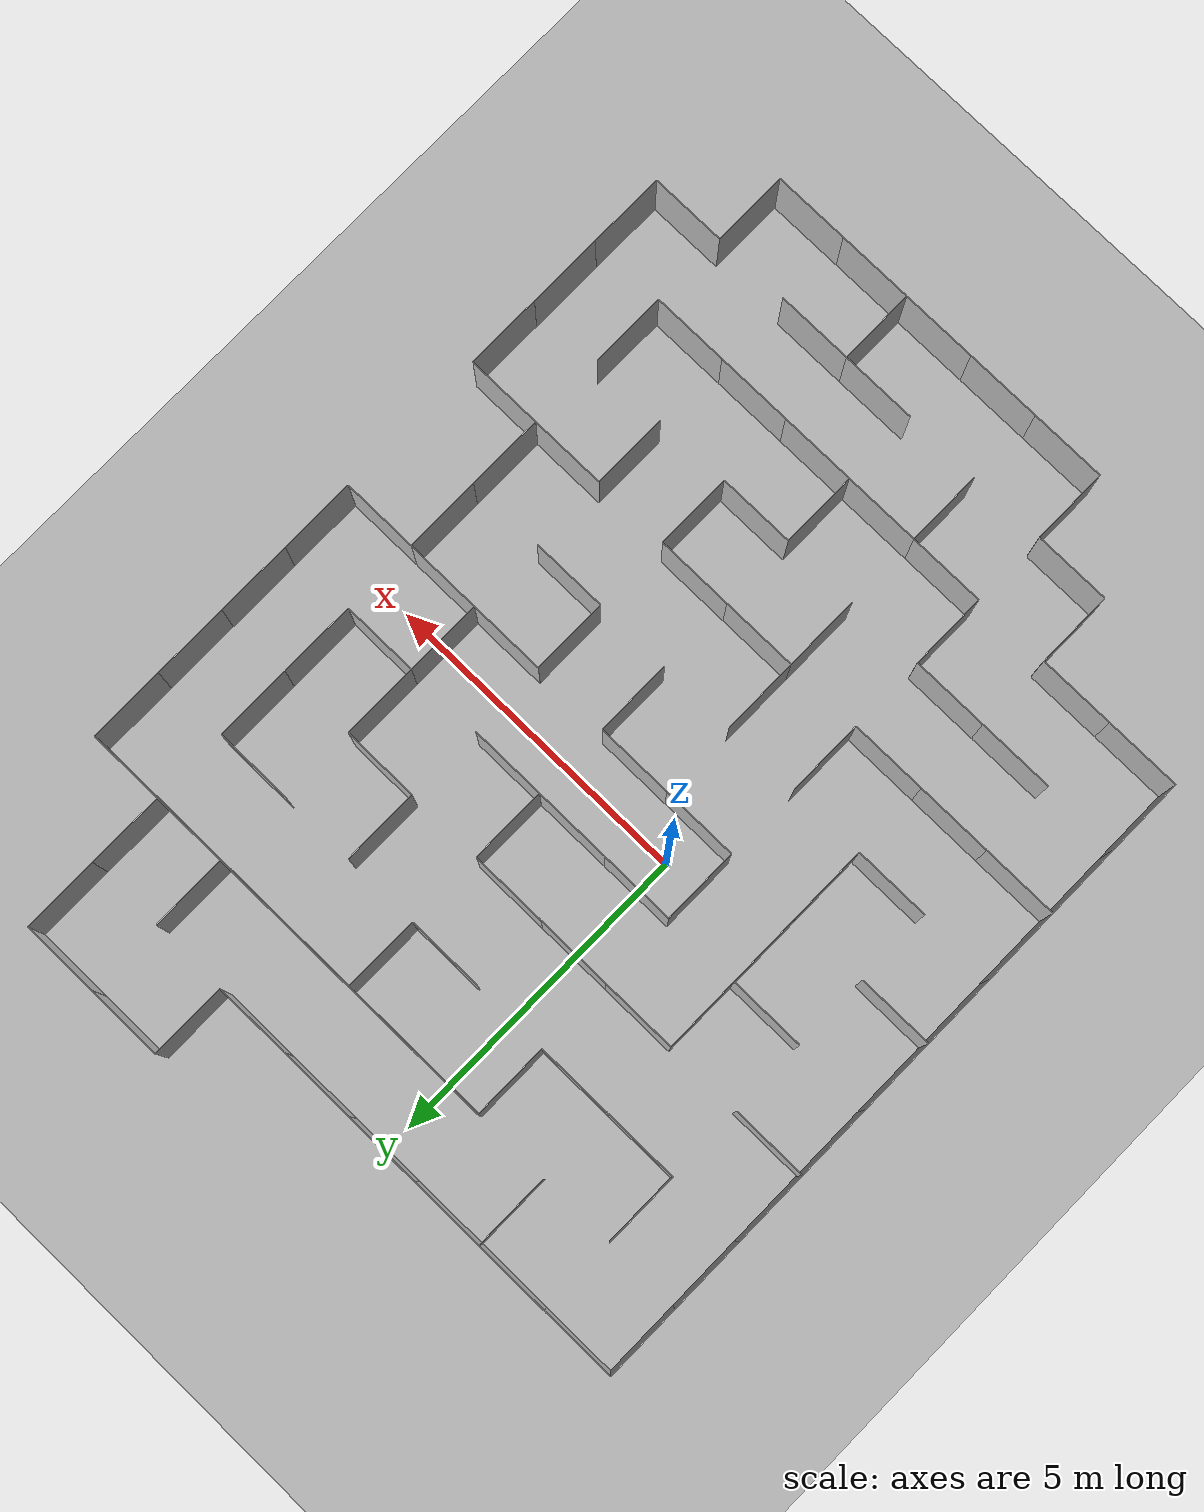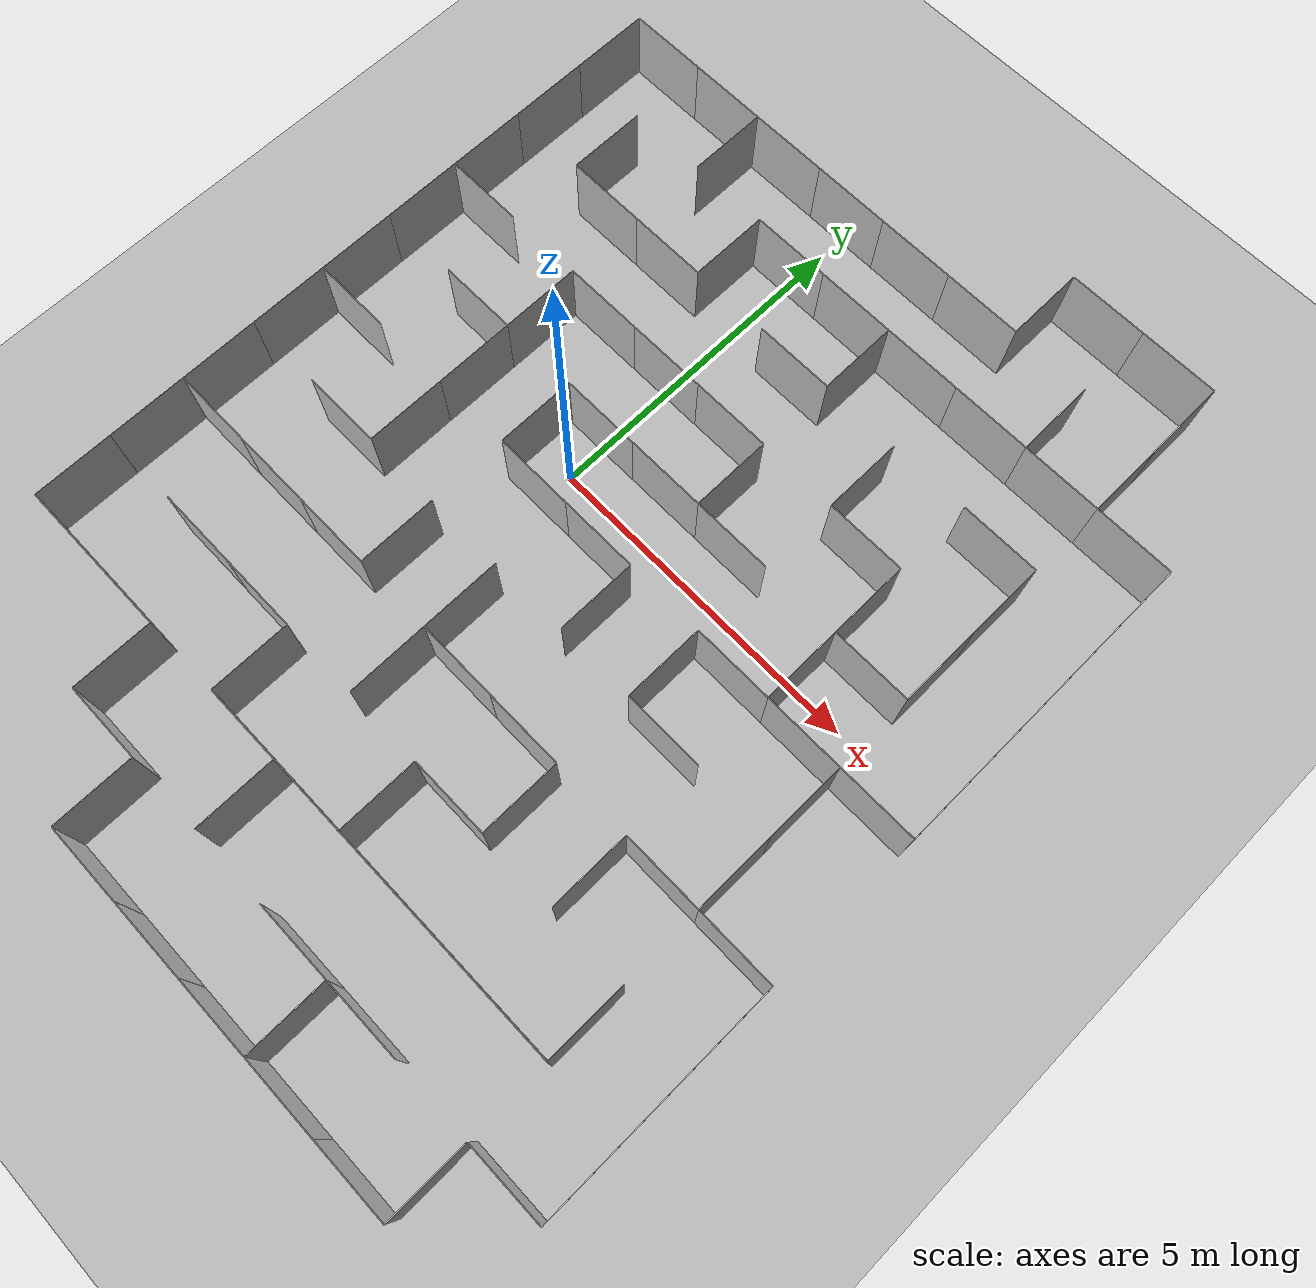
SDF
<?xml version="1.0" encoding="UTF-8" ?>
<sdf version="1.4">
  <world name="default">
    <scene>
      <ambient>0.5 0.5 0.5 1</ambient>
      <background>0.5 0.5 0.5 1</background>
      <shadows>false</shadows>
    </scene>
    <physics type="ode">
      <gravity>0 0 -9.81</gravity>
      <ode>
        <solver>
          <type>quick</type>
          <iters>10</iters>
          <sor>1.3</sor>
        </solver>
        <constraints>
          <cfm>0.0</cfm>
          <erp>0.2</erp>
          <contact_max_correcting_vel>100.0</contact_max_correcting_vel>
          <contact_surface_layer>0.001</contact_surface_layer>
        </constraints>
      </ode>
      <real_time_update_rate>1000</real_time_update_rate>
      <max_step_size>0.001</max_step_size>
    </physics>
    <light type="directional" name="directional_light_1">
      <cast_shadows>false</cast_shadows>
      <pose>0 0 30 0.1 0.1 0</pose>
      <diffuse>1.0 1.0 1.0 1</diffuse>
      <specular>.1 .1 .1 1</specular>
      <attenuation>
        <range>300</range>
      </attenuation>
      <direction>0.1 0.1 -1</direction>
    </light>
    <model name="plane_model">
      <static>true</static>
      <link name="plane_model_link">
        <collision name="plane_model_collision">
          <geometry>
            <plane>
              <normal>0 0 1</normal>
            </plane>
          </geometry>
          <surface>
            <friction>
              <ode>
                <mu>10.0</mu>
                <mu2>10.0</mu2>
                <fdir1>0 0 0</fdir1>
                <slip1>0</slip1>
                <slip2>0</slip2>
              </ode>
            </friction>
            <bounce>
              <restitution_coefficient>0</restitution_coefficient>
              <threshold>1000000.0</threshold>
            </bounce>
            <contact>
              <ode>
                <soft_cfm>0</soft_cfm>
                <soft_erp>0.2</soft_erp>
                <kp>1e10</kp>
                <kd>1</kd>
                <max_vel>100.0</max_vel>
                <min_depth>0.0001</min_depth>
              </ode>
            </contact>
          </surface>
        </collision>
        <visual name="plane_model_visual">
          <cast_shadows>false</cast_shadows>
          <geometry>
            <mesh>
              <uri>model://ground_plane/ground_plane.dae</uri>
              <scale>1 1 1</scale>
            </mesh>
          </geometry>
        </visual>
      </link>
    </model>
    <model name="small_wall_61">
      <static>true</static>
      <link name="small_wall_61_link">
        <pose>0 0 0 0 0 -4.71239</pose>
        <collision name="small_wall_61_collision">
          <geometry>
            <mesh>
              <uri>model://small_wall/meshes/small_wall.dae</uri>
              <scale>1 1 1</scale>
            </mesh>
          </geometry>
        </collision>
        <visual name="small_wall_61_visual">
          <cast_shadows>false</cast_shadows>
          <geometry>
            <mesh>
              <uri>model://small_wall/meshes/small_wall.dae</uri>
              <scale>1 1 1</scale>
            </mesh>
          </geometry>
        </visual>
      </link>
    </model>
    <model name="small_wall_62">
      <static>true</static>
      <link name="small_wall_62_link">
        <pose>0 1.2 0 0 0 -3.14159</pose>
        <collision name="small_wall_62_collision">
          <geometry>
            <mesh>
              <uri>model://small_wall/meshes/small_wall.dae</uri>
              <scale>1 1 1</scale>
            </mesh>
          </geometry>
        </collision>
        <visual name="small_wall_62_visual">
          <cast_shadows>false</cast_shadows>
          <geometry>
            <mesh>
              <uri>model://small_wall/meshes/small_wall.dae</uri>
              <scale>1 1 1</scale>
            </mesh>
          </geometry>
        </visual>
      </link>
    </model>
    <model name="small_wall_63">
      <static>true</static>
      <link name="small_wall_63_link">
        <pose>1.2 1.2 0 0 0 -3.14159</pose>
        <collision name="small_wall_63_collision">
          <geometry>
            <mesh>
              <uri>model://small_wall/meshes/small_wall.dae</uri>
              <scale>1 1 1</scale>
            </mesh>
          </geometry>
        </collision>
        <visual name="small_wall_63_visual">
          <cast_shadows>false</cast_shadows>
          <geometry>
            <mesh>
              <uri>model://small_wall/meshes/small_wall.dae</uri>
              <scale>1 1 1</scale>
            </mesh>
          </geometry>
        </visual>
      </link>
    </model>
    <model name="small_wall_64">
      <static>true</static>
      <link name="small_wall_64_link">
        <pose>0 0 0 0 0 -3.14159</pose>
        <collision name="small_wall_64_collision">
          <geometry>
            <mesh>
              <uri>model://small_wall/meshes/small_wall.dae</uri>
              <scale>1 1 1</scale>
            </mesh>
          </geometry>
        </collision>
        <visual name="small_wall_64_visual">
          <cast_shadows>false</cast_shadows>
          <geometry>
            <mesh>
              <uri>model://small_wall/meshes/small_wall.dae</uri>
              <scale>1 1 1</scale>
            </mesh>
          </geometry>
        </visual>
      </link>
    </model>
    <model name="small_wall_65">
      <static>true</static>
      <link name="small_wall_65_link">
        <pose>1.2 0 0 0 0 -3.14159</pose>
        <collision name="small_wall_65_collision">
          <geometry>
            <mesh>
              <uri>model://small_wall/meshes/small_wall.dae</uri>
              <scale>1 1 1</scale>
            </mesh>
          </geometry>
        </collision>
        <visual name="small_wall_65_visual">
          <cast_shadows>false</cast_shadows>
          <geometry>
            <mesh>
              <uri>model://small_wall/meshes/small_wall.dae</uri>
              <scale>1 1 1</scale>
            </mesh>
          </geometry>
        </visual>
      </link>
    </model>
    <model name="small_wall_66">
      <static>true</static>
      <link name="small_wall_66_link">
        <pose>2.4 -1.2 0 0 0 -4.71239</pose>
        <collision name="small_wall_66_collision">
          <geometry>
            <mesh>
              <uri>model://small_wall/meshes/small_wall.dae</uri>
              <scale>1 1 1</scale>
            </mesh>
          </geometry>
        </collision>
        <visual name="small_wall_66_visual">
          <cast_shadows>false</cast_shadows>
          <geometry>
            <mesh>
              <uri>model://small_wall/meshes/small_wall.dae</uri>
              <scale>1 1 1</scale>
            </mesh>
          </geometry>
        </visual>
      </link>
    </model>
    <model name="small_wall_67">
      <static>true</static>
      <link name="small_wall_67_link">
        <pose>2.4 -1.2 0 0 0 -1.5708</pose>
        <collision name="small_wall_67_collision">
          <geometry>
            <mesh>
              <uri>model://small_wall/meshes/small_wall.dae</uri>
              <scale>1 1 1</scale>
            </mesh>
          </geometry>
        </collision>
        <visual name="small_wall_67_visual">
          <cast_shadows>false</cast_shadows>
          <geometry>
            <mesh>
              <uri>model://small_wall/meshes/small_wall.dae</uri>
              <scale>1 1 1</scale>
            </mesh>
          </geometry>
        </visual>
      </link>
    </model>
    <model name="small_wall_68">
      <static>true</static>
      <link name="small_wall_68_link">
        <pose>3.6 0 0 0 0 -3.14159</pose>
        <collision name="small_wall_68_collision">
          <geometry>
            <mesh>
              <uri>model://small_wall/meshes/small_wall.dae</uri>
              <scale>1 1 1</scale>
            </mesh>
          </geometry>
        </collision>
        <visual name="small_wall_68_visual">
          <cast_shadows>false</cast_shadows>
          <geometry>
            <mesh>
              <uri>model://small_wall/meshes/small_wall.dae</uri>
              <scale>1 1 1</scale>
            </mesh>
          </geometry>
        </visual>
      </link>
    </model>
    <model name="small_wall_69">
      <static>true</static>
      <link name="small_wall_69_link">
        <pose>3.6 0 0 0 0 -1.5708</pose>
        <collision name="small_wall_69_collision">
          <geometry>
            <mesh>
              <uri>model://small_wall/meshes/small_wall.dae</uri>
              <scale>1 1 1</scale>
            </mesh>
          </geometry>
        </collision>
        <visual name="small_wall_69_visual">
          <cast_shadows>false</cast_shadows>
          <geometry>
            <mesh>
              <uri>model://small_wall/meshes/small_wall.dae</uri>
              <scale>1 1 1</scale>
            </mesh>
          </geometry>
        </visual>
      </link>
    </model>
    <model name="small_wall_70">
      <static>true</static>
      <link name="small_wall_70_link">
        <pose>2.4 1.2 0 0 0 -3.14159</pose>
        <collision name="small_wall_70_collision">
          <geometry>
            <mesh>
              <uri>model://small_wall/meshes/small_wall.dae</uri>
              <scale>1 1 1</scale>
            </mesh>
          </geometry>
        </collision>
        <visual name="small_wall_70_visual">
          <cast_shadows>false</cast_shadows>
          <geometry>
            <mesh>
              <uri>model://small_wall/meshes/small_wall.dae</uri>
              <scale>1 1 1</scale>
            </mesh>
          </geometry>
        </visual>
      </link>
    </model>
    <model name="small_wall_71">
      <static>true</static>
      <link name="small_wall_71_link">
        <pose>3.6 1.2 0 0 0 -1.5708</pose>
        <collision name="small_wall_71_collision">
          <geometry>
            <mesh>
              <uri>model://small_wall/meshes/small_wall.dae</uri>
              <scale>1 1 1</scale>
            </mesh>
          </geometry>
        </collision>
        <visual name="small_wall_71_visual">
          <cast_shadows>false</cast_shadows>
          <geometry>
            <mesh>
              <uri>model://small_wall/meshes/small_wall.dae</uri>
              <scale>1 1 1</scale>
            </mesh>
          </geometry>
        </visual>
      </link>
    </model>
    <model name="small_wall_72">
      <static>true</static>
      <link name="small_wall_72_link">
        <pose>3.6 1.2 0 0 0 0</pose>
        <collision name="small_wall_72_collision">
          <geometry>
            <mesh>
              <uri>model://small_wall/meshes/small_wall.dae</uri>
              <scale>1 1 1</scale>
            </mesh>
          </geometry>
        </collision>
        <visual name="small_wall_72_visual">
          <cast_shadows>false</cast_shadows>
          <geometry>
            <mesh>
              <uri>model://small_wall/meshes/small_wall.dae</uri>
              <scale>1 1 1</scale>
            </mesh>
          </geometry>
        </visual>
      </link>
    </model>
    <model name="small_wall_73">
      <static>true</static>
      <link name="small_wall_73_link">
        <pose>2.4 1.2 0 0 0 -4.71239</pose>
        <collision name="small_wall_73_collision">
          <geometry>
            <mesh>
              <uri>model://small_wall/meshes/small_wall.dae</uri>
              <scale>1 1 1</scale>
            </mesh>
          </geometry>
        </collision>
        <visual name="small_wall_73_visual">
          <cast_shadows>false</cast_shadows>
          <geometry>
            <mesh>
              <uri>model://small_wall/meshes/small_wall.dae</uri>
              <scale>1 1 1</scale>
            </mesh>
          </geometry>
        </visual>
      </link>
    </model>
    <model name="small_wall_74">
      <static>true</static>
      <link name="small_wall_74_link">
        <pose>3.6 2.4 0 0 0 -4.71239</pose>
        <collision name="small_wall_74_collision">
          <geometry>
            <mesh>
              <uri>model://small_wall/meshes/small_wall.dae</uri>
              <scale>1 1 1</scale>
            </mesh>
          </geometry>
        </collision>
        <visual name="small_wall_74_visual">
          <cast_shadows>false</cast_shadows>
          <geometry>
            <mesh>
              <uri>model://small_wall/meshes/small_wall.dae</uri>
              <scale>1 1 1</scale>
            </mesh>
          </geometry>
        </visual>
      </link>
    </model>
    <model name="small_wall_75">
      <static>true</static>
      <link name="small_wall_75_link">
        <pose>1.2 2.4 0 0 0 -3.14159</pose>
        <collision name="small_wall_75_collision">
          <geometry>
            <mesh>
              <uri>model://small_wall/meshes/small_wall.dae</uri>
              <scale>1 1 1</scale>
            </mesh>
          </geometry>
        </collision>
        <visual name="small_wall_75_visual">
          <cast_shadows>false</cast_shadows>
          <geometry>
            <mesh>
              <uri>model://small_wall/meshes/small_wall.dae</uri>
              <scale>1 1 1</scale>
            </mesh>
          </geometry>
        </visual>
      </link>
    </model>
    <model name="small_wall_76">
      <static>true</static>
      <link name="small_wall_76_link">
        <pose>0 2.4 0 0 0 -3.14159</pose>
        <collision name="small_wall_76_collision">
          <geometry>
            <mesh>
              <uri>model://small_wall/meshes/small_wall.dae</uri>
              <scale>1 1 1</scale>
            </mesh>
          </geometry>
        </collision>
        <visual name="small_wall_76_visual">
          <cast_shadows>false</cast_shadows>
          <geometry>
            <mesh>
              <uri>model://small_wall/meshes/small_wall.dae</uri>
              <scale>1 1 1</scale>
            </mesh>
          </geometry>
        </visual>
      </link>
    </model>
    <model name="small_wall_77">
      <static>true</static>
      <link name="small_wall_77_link">
        <pose>-1.2 1.2 0 0 0 0</pose>
        <collision name="small_wall_77_collision">
          <geometry>
            <mesh>
              <uri>model://small_wall/meshes/small_wall.dae</uri>
              <scale>1 1 1</scale>
            </mesh>
          </geometry>
        </collision>
        <visual name="small_wall_77_visual">
          <cast_shadows>false</cast_shadows>
          <geometry>
            <mesh>
              <uri>model://small_wall/meshes/small_wall.dae</uri>
              <scale>1 1 1</scale>
            </mesh>
          </geometry>
        </visual>
      </link>
    </model>
    <model name="small_wall_78">
      <static>true</static>
      <link name="small_wall_78_link">
        <pose>-1.2 1.2 0 0 0 -4.71239</pose>
        <collision name="small_wall_78_collision">
          <geometry>
            <mesh>
              <uri>model://small_wall/meshes/small_wall.dae</uri>
              <scale>1 1 1</scale>
            </mesh>
          </geometry>
        </collision>
        <visual name="small_wall_78_visual">
          <cast_shadows>false</cast_shadows>
          <geometry>
            <mesh>
              <uri>model://small_wall/meshes/small_wall.dae</uri>
              <scale>1 1 1</scale>
            </mesh>
          </geometry>
        </visual>
      </link>
    </model>
    <model name="small_wall_79">
      <static>true</static>
      <link name="small_wall_79_link">
        <pose>-2.4 0 0 0 0 -1.5708</pose>
        <collision name="small_wall_79_collision">
          <geometry>
            <mesh>
              <uri>model://small_wall/meshes/small_wall.dae</uri>
              <scale>1 1 1</scale>
            </mesh>
          </geometry>
        </collision>
        <visual name="small_wall_79_visual">
          <cast_shadows>false</cast_shadows>
          <geometry>
            <mesh>
              <uri>model://small_wall/meshes/small_wall.dae</uri>
              <scale>1 1 1</scale>
            </mesh>
          </geometry>
        </visual>
      </link>
    </model>
    <model name="small_wall_80">
      <static>true</static>
      <link name="small_wall_80_link">
        <pose>1.2 3.6 0 0 0 -3.14159</pose>
        <collision name="small_wall_80_collision">
          <geometry>
            <mesh>
              <uri>model://small_wall/meshes/small_wall.dae</uri>
              <scale>1 1 1</scale>
            </mesh>
          </geometry>
        </collision>
        <visual name="small_wall_80_visual">
          <cast_shadows>false</cast_shadows>
          <geometry>
            <mesh>
              <uri>model://small_wall/meshes/small_wall.dae</uri>
              <scale>1 1 1</scale>
            </mesh>
          </geometry>
        </visual>
      </link>
    </model>
    <model name="small_wall_81">
      <static>true</static>
      <link name="small_wall_81_link">
        <pose>2.4 3.6 0 0 0 -4.71239</pose>
        <collision name="small_wall_81_collision">
          <geometry>
            <mesh>
              <uri>model://small_wall/meshes/small_wall.dae</uri>
              <scale>1 1 1</scale>
            </mesh>
          </geometry>
        </collision>
        <visual name="small_wall_81_visual">
          <cast_shadows>false</cast_shadows>
          <geometry>
            <mesh>
              <uri>model://small_wall/meshes/small_wall.dae</uri>
              <scale>1 1 1</scale>
            </mesh>
          </geometry>
        </visual>
      </link>
    </model>
    <model name="small_wall_82">
      <static>true</static>
      <link name="small_wall_82_link">
        <pose>2.4 3.6 0 0 0 0</pose>
        <collision name="small_wall_82_collision">
          <geometry>
            <mesh>
              <uri>model://small_wall/meshes/small_wall.dae</uri>
              <scale>1 1 1</scale>
            </mesh>
          </geometry>
        </collision>
        <visual name="small_wall_82_visual">
          <cast_shadows>false</cast_shadows>
          <geometry>
            <mesh>
              <uri>model://small_wall/meshes/small_wall.dae</uri>
              <scale>1 1 1</scale>
            </mesh>
          </geometry>
        </visual>
      </link>
    </model>
    <model name="small_wall_83">
      <static>true</static>
      <link name="small_wall_83_link">
        <pose>3.6 3.6 0 0 0 0</pose>
        <collision name="small_wall_83_collision">
          <geometry>
            <mesh>
              <uri>model://small_wall/meshes/small_wall.dae</uri>
              <scale>1 1 1</scale>
            </mesh>
          </geometry>
        </collision>
        <visual name="small_wall_83_visual">
          <cast_shadows>false</cast_shadows>
          <geometry>
            <mesh>
              <uri>model://small_wall/meshes/small_wall.dae</uri>
              <scale>1 1 1</scale>
            </mesh>
          </geometry>
        </visual>
      </link>
    </model>
    <model name="small_wall_84">
      <static>true</static>
      <link name="small_wall_84_link">
        <pose>4.8 2.4 0 0 0 0</pose>
        <collision name="small_wall_84_collision">
          <geometry>
            <mesh>
              <uri>model://small_wall/meshes/small_wall.dae</uri>
              <scale>1 1 1</scale>
            </mesh>
          </geometry>
        </collision>
        <visual name="small_wall_84_visual">
          <cast_shadows>false</cast_shadows>
          <geometry>
            <mesh>
              <uri>model://small_wall/meshes/small_wall.dae</uri>
              <scale>1 1 1</scale>
            </mesh>
          </geometry>
        </visual>
      </link>
    </model>
    <model name="small_wall_85">
      <static>true</static>
      <link name="small_wall_85_link">
        <pose>4.8 3.6 0 0 0 0</pose>
        <collision name="small_wall_85_collision">
          <geometry>
            <mesh>
              <uri>model://small_wall/meshes/small_wall.dae</uri>
              <scale>1 1 1</scale>
            </mesh>
          </geometry>
        </collision>
        <visual name="small_wall_85_visual">
          <cast_shadows>false</cast_shadows>
          <geometry>
            <mesh>
              <uri>model://small_wall/meshes/small_wall.dae</uri>
              <scale>1 1 1</scale>
            </mesh>
          </geometry>
        </visual>
      </link>
    </model>
    <model name="small_wall_86">
      <static>true</static>
      <link name="small_wall_86_link">
        <pose>4.8 2.4 0 0 0 -1.5708</pose>
        <collision name="small_wall_86_collision">
          <geometry>
            <mesh>
              <uri>model://small_wall/meshes/small_wall.dae</uri>
              <scale>1 1 1</scale>
            </mesh>
          </geometry>
        </collision>
        <visual name="small_wall_86_visual">
          <cast_shadows>false</cast_shadows>
          <geometry>
            <mesh>
              <uri>model://small_wall/meshes/small_wall.dae</uri>
              <scale>1 1 1</scale>
            </mesh>
          </geometry>
        </visual>
      </link>
    </model>
    <model name="small_wall_87">
      <static>true</static>
      <link name="small_wall_87_link">
        <pose>4.8 1.2 0 0 0 -1.5708</pose>
        <collision name="small_wall_87_collision">
          <geometry>
            <mesh>
              <uri>model://small_wall/meshes/small_wall.dae</uri>
              <scale>1 1 1</scale>
            </mesh>
          </geometry>
        </collision>
        <visual name="small_wall_87_visual">
          <cast_shadows>false</cast_shadows>
          <geometry>
            <mesh>
              <uri>model://small_wall/meshes/small_wall.dae</uri>
              <scale>1 1 1</scale>
            </mesh>
          </geometry>
        </visual>
      </link>
    </model>
    <model name="small_wall_88">
      <static>true</static>
      <link name="small_wall_88_link">
        <pose>4.8 1.2 0 0 0 -3.14159</pose>
        <collision name="small_wall_88_collision">
          <geometry>
            <mesh>
              <uri>model://small_wall/meshes/small_wall.dae</uri>
              <scale>1 1 1</scale>
            </mesh>
          </geometry>
        </collision>
        <visual name="small_wall_88_visual">
          <cast_shadows>false</cast_shadows>
          <geometry>
            <mesh>
              <uri>model://small_wall/meshes/small_wall.dae</uri>
              <scale>1 1 1</scale>
            </mesh>
          </geometry>
        </visual>
      </link>
    </model>
    <model name="small_wall_89">
      <static>true</static>
      <link name="small_wall_89_link">
        <pose>-1.2 -1.2 0 0 0 -4.71239</pose>
        <collision name="small_wall_89_collision">
          <geometry>
            <mesh>
              <uri>model://small_wall/meshes/small_wall.dae</uri>
              <scale>1 1 1</scale>
            </mesh>
          </geometry>
        </collision>
        <visual name="small_wall_89_visual">
          <cast_shadows>false</cast_shadows>
          <geometry>
            <mesh>
              <uri>model://small_wall/meshes/small_wall.dae</uri>
              <scale>1 1 1</scale>
            </mesh>
          </geometry>
        </visual>
      </link>
    </model>
    <model name="small_wall_90">
      <static>true</static>
      <link name="small_wall_90_link">
        <pose>0 -2.4 0 0 0 -4.71239</pose>
        <collision name="small_wall_90_collision">
          <geometry>
            <mesh>
              <uri>model://small_wall/meshes/small_wall.dae</uri>
              <scale>1 1 1</scale>
            </mesh>
          </geometry>
        </collision>
        <visual name="small_wall_90_visual">
          <cast_shadows>false</cast_shadows>
          <geometry>
            <mesh>
              <uri>model://small_wall/meshes/small_wall.dae</uri>
              <scale>1 1 1</scale>
            </mesh>
          </geometry>
        </visual>
      </link>
    </model>
    <model name="small_wall_91">
      <static>true</static>
      <link name="small_wall_91_link">
        <pose>0 -2.4 0 0 0 -1.5708</pose>
        <collision name="small_wall_91_collision">
          <geometry>
            <mesh>
              <uri>model://small_wall/meshes/small_wall.dae</uri>
              <scale>1 1 1</scale>
            </mesh>
          </geometry>
        </collision>
        <visual name="small_wall_91_visual">
          <cast_shadows>false</cast_shadows>
          <geometry>
            <mesh>
              <uri>model://small_wall/meshes/small_wall.dae</uri>
              <scale>1 1 1</scale>
            </mesh>
          </geometry>
        </visual>
      </link>
    </model>
    <model name="small_wall_92">
      <static>true</static>
      <link name="small_wall_92_link">
        <pose>1.2 -2.4 0 0 0 -3.14159</pose>
        <collision name="small_wall_92_collision">
          <geometry>
            <mesh>
              <uri>model://small_wall/meshes/small_wall.dae</uri>
              <scale>1 1 1</scale>
            </mesh>
          </geometry>
        </collision>
        <visual name="small_wall_92_visual">
          <cast_shadows>false</cast_shadows>
          <geometry>
            <mesh>
              <uri>model://small_wall/meshes/small_wall.dae</uri>
              <scale>1 1 1</scale>
            </mesh>
          </geometry>
        </visual>
      </link>
    </model>
    <model name="small_wall_93">
      <static>true</static>
      <link name="small_wall_93_link">
        <pose>2.4 -2.4 0 0 0 -3.14159</pose>
        <collision name="small_wall_93_collision">
          <geometry>
            <mesh>
              <uri>model://small_wall/meshes/small_wall.dae</uri>
              <scale>1 1 1</scale>
            </mesh>
          </geometry>
        </collision>
        <visual name="small_wall_93_visual">
          <cast_shadows>false</cast_shadows>
          <geometry>
            <mesh>
              <uri>model://small_wall/meshes/small_wall.dae</uri>
              <scale>1 1 1</scale>
            </mesh>
          </geometry>
        </visual>
      </link>
    </model>
    <model name="small_wall_94">
      <static>true</static>
      <link name="small_wall_94_link">
        <pose>3.6 -3.6 0 0 0 -4.71239</pose>
        <collision name="small_wall_94_collision">
          <geometry>
            <mesh>
              <uri>model://small_wall/meshes/small_wall.dae</uri>
              <scale>1 1 1</scale>
            </mesh>
          </geometry>
        </collision>
        <visual name="small_wall_94_visual">
          <cast_shadows>false</cast_shadows>
          <geometry>
            <mesh>
              <uri>model://small_wall/meshes/small_wall.dae</uri>
              <scale>1 1 1</scale>
            </mesh>
          </geometry>
        </visual>
      </link>
    </model>
    <model name="small_wall_95">
      <static>true</static>
      <link name="small_wall_95_link">
        <pose>3.6 -1.2 0 0 0 -3.14159</pose>
        <collision name="small_wall_95_collision">
          <geometry>
            <mesh>
              <uri>model://small_wall/meshes/small_wall.dae</uri>
              <scale>1 1 1</scale>
            </mesh>
          </geometry>
        </collision>
        <visual name="small_wall_95_visual">
          <cast_shadows>false</cast_shadows>
          <geometry>
            <mesh>
              <uri>model://small_wall/meshes/small_wall.dae</uri>
              <scale>1 1 1</scale>
            </mesh>
          </geometry>
        </visual>
      </link>
    </model>
    <model name="small_wall_96">
      <static>true</static>
      <link name="small_wall_96_link">
        <pose>6 -2.4 0 0 0 -4.71239</pose>
        <collision name="small_wall_96_collision">
          <geometry>
            <mesh>
              <uri>model://small_wall/meshes/small_wall.dae</uri>
              <scale>1 1 1</scale>
            </mesh>
          </geometry>
        </collision>
        <visual name="small_wall_96_visual">
          <cast_shadows>false</cast_shadows>
          <geometry>
            <mesh>
              <uri>model://small_wall/meshes/small_wall.dae</uri>
              <scale>1 1 1</scale>
            </mesh>
          </geometry>
        </visual>
      </link>
    </model>
    <model name="small_wall_97">
      <static>true</static>
      <link name="small_wall_97_link">
        <pose>4.8 -1.2 0 0 0 0</pose>
        <collision name="small_wall_97_collision">
          <geometry>
            <mesh>
              <uri>model://small_wall/meshes/small_wall.dae</uri>
              <scale>1 1 1</scale>
            </mesh>
          </geometry>
        </collision>
        <visual name="small_wall_97_visual">
          <cast_shadows>false</cast_shadows>
          <geometry>
            <mesh>
              <uri>model://small_wall/meshes/small_wall.dae</uri>
              <scale>1 1 1</scale>
            </mesh>
          </geometry>
        </visual>
      </link>
    </model>
    <model name="small_wall_98">
      <static>true</static>
      <link name="small_wall_98_link">
        <pose>4.8 -1.2 0 0 0 -1.5708</pose>
        <collision name="small_wall_98_collision">
          <geometry>
            <mesh>
              <uri>model://small_wall/meshes/small_wall.dae</uri>
              <scale>1 1 1</scale>
            </mesh>
          </geometry>
        </collision>
        <visual name="small_wall_98_visual">
          <cast_shadows>false</cast_shadows>
          <geometry>
            <mesh>
              <uri>model://small_wall/meshes/small_wall.dae</uri>
              <scale>1 1 1</scale>
            </mesh>
          </geometry>
        </visual>
      </link>
    </model>
    <model name="small_wall_99">
      <static>true</static>
      <link name="small_wall_99_link">
        <pose>4.8 -2.4 0 0 0 -3.14159</pose>
        <collision name="small_wall_99_collision">
          <geometry>
            <mesh>
              <uri>model://small_wall/meshes/small_wall.dae</uri>
              <scale>1 1 1</scale>
            </mesh>
          </geometry>
        </collision>
        <visual name="small_wall_99_visual">
          <cast_shadows>false</cast_shadows>
          <geometry>
            <mesh>
              <uri>model://small_wall/meshes/small_wall.dae</uri>
              <scale>1 1 1</scale>
            </mesh>
          </geometry>
        </visual>
      </link>
    </model>
    <model name="small_wall_100">
      <static>true</static>
      <link name="small_wall_100_link">
        <pose>6 4.8 0 0 0 -3.14159</pose>
        <collision name="small_wall_100_collision">
          <geometry>
            <mesh>
              <uri>model://small_wall/meshes/small_wall.dae</uri>
              <scale>1 1 1</scale>
            </mesh>
          </geometry>
        </collision>
        <visual name="small_wall_100_visual">
          <cast_shadows>false</cast_shadows>
          <geometry>
            <mesh>
              <uri>model://small_wall/meshes/small_wall.dae</uri>
              <scale>1 1 1</scale>
            </mesh>
          </geometry>
        </visual>
      </link>
    </model>
    <model name="small_wall_101">
      <static>true</static>
      <link name="small_wall_101_link">
        <pose>6 3.6 0 0 0 -1.5708</pose>
        <collision name="small_wall_101_collision">
          <geometry>
            <mesh>
              <uri>model://small_wall/meshes/small_wall.dae</uri>
              <scale>1 1 1</scale>
            </mesh>
          </geometry>
        </collision>
        <visual name="small_wall_101_visual">
          <cast_shadows>false</cast_shadows>
          <geometry>
            <mesh>
              <uri>model://small_wall/meshes/small_wall.dae</uri>
              <scale>1 1 1</scale>
            </mesh>
          </geometry>
        </visual>
      </link>
    </model>
    <model name="small_wall_102">
      <static>true</static>
      <link name="small_wall_102_link">
        <pose>6 2.4 0 0 0 -1.5708</pose>
        <collision name="small_wall_102_collision">
          <geometry>
            <mesh>
              <uri>model://small_wall/meshes/small_wall.dae</uri>
              <scale>1 1 1</scale>
            </mesh>
          </geometry>
        </collision>
        <visual name="small_wall_102_visual">
          <cast_shadows>false</cast_shadows>
          <geometry>
            <mesh>
              <uri>model://small_wall/meshes/small_wall.dae</uri>
              <scale>1 1 1</scale>
            </mesh>
          </geometry>
        </visual>
      </link>
    </model>
    <model name="small_wall_103">
      <static>true</static>
      <link name="small_wall_103_link">
        <pose>6 1.2 0 0 0 -1.5708</pose>
        <collision name="small_wall_103_collision">
          <geometry>
            <mesh>
              <uri>model://small_wall/meshes/small_wall.dae</uri>
              <scale>1 1 1</scale>
            </mesh>
          </geometry>
        </collision>
        <visual name="small_wall_103_visual">
          <cast_shadows>false</cast_shadows>
          <geometry>
            <mesh>
              <uri>model://small_wall/meshes/small_wall.dae</uri>
              <scale>1 1 1</scale>
            </mesh>
          </geometry>
        </visual>
      </link>
    </model>
    <model name="small_wall_104">
      <static>true</static>
      <link name="small_wall_104_link">
        <pose>6 0 0 0 0 -1.5708</pose>
        <collision name="small_wall_104_collision">
          <geometry>
            <mesh>
              <uri>model://small_wall/meshes/small_wall.dae</uri>
              <scale>1 1 1</scale>
            </mesh>
          </geometry>
        </collision>
        <visual name="small_wall_104_visual">
          <cast_shadows>false</cast_shadows>
          <geometry>
            <mesh>
              <uri>model://small_wall/meshes/small_wall.dae</uri>
              <scale>1 1 1</scale>
            </mesh>
          </geometry>
        </visual>
      </link>
    </model>
    <model name="small_wall_105">
      <static>true</static>
      <link name="small_wall_105_link">
        <pose>6 0 0 0 0 -3.14159</pose>
        <collision name="small_wall_105_collision">
          <geometry>
            <mesh>
              <uri>model://small_wall/meshes/small_wall.dae</uri>
              <scale>1 1 1</scale>
            </mesh>
          </geometry>
        </collision>
        <visual name="small_wall_105_visual">
          <cast_shadows>false</cast_shadows>
          <geometry>
            <mesh>
              <uri>model://small_wall/meshes/small_wall.dae</uri>
              <scale>1 1 1</scale>
            </mesh>
          </geometry>
        </visual>
      </link>
    </model>
    <model name="small_wall_106">
      <static>true</static>
      <link name="small_wall_106_link">
        <pose>-1.2 3.6 0 0 0 -3.14159</pose>
        <collision name="small_wall_106_collision">
          <geometry>
            <mesh>
              <uri>model://small_wall/meshes/small_wall.dae</uri>
              <scale>1 1 1</scale>
            </mesh>
          </geometry>
        </collision>
        <visual name="small_wall_106_visual">
          <cast_shadows>false</cast_shadows>
          <geometry>
            <mesh>
              <uri>model://small_wall/meshes/small_wall.dae</uri>
              <scale>1 1 1</scale>
            </mesh>
          </geometry>
        </visual>
      </link>
    </model>
    <model name="small_wall_107">
      <static>true</static>
      <link name="small_wall_107_link">
        <pose>-1.2 3.6 0 0 0 -1.5708</pose>
        <collision name="small_wall_107_collision">
          <geometry>
            <mesh>
              <uri>model://small_wall/meshes/small_wall.dae</uri>
              <scale>1 1 1</scale>
            </mesh>
          </geometry>
        </collision>
        <visual name="small_wall_107_visual">
          <cast_shadows>false</cast_shadows>
          <geometry>
            <mesh>
              <uri>model://small_wall/meshes/small_wall.dae</uri>
              <scale>1 1 1</scale>
            </mesh>
          </geometry>
        </visual>
      </link>
    </model>
    <model name="small_wall_108">
      <static>true</static>
      <link name="small_wall_108_link">
        <pose>0 4.8 0 0 0 -3.14159</pose>
        <collision name="small_wall_108_collision">
          <geometry>
            <mesh>
              <uri>model://small_wall/meshes/small_wall.dae</uri>
              <scale>1 1 1</scale>
            </mesh>
          </geometry>
        </collision>
        <visual name="small_wall_108_visual">
          <cast_shadows>false</cast_shadows>
          <geometry>
            <mesh>
              <uri>model://small_wall/meshes/small_wall.dae</uri>
              <scale>1 1 1</scale>
            </mesh>
          </geometry>
        </visual>
      </link>
    </model>
    <model name="small_wall_109">
      <static>true</static>
      <link name="small_wall_109_link">
        <pose>1.2 4.8 0 0 0 -3.14159</pose>
        <collision name="small_wall_109_collision">
          <geometry>
            <mesh>
              <uri>model://small_wall/meshes/small_wall.dae</uri>
              <scale>1 1 1</scale>
            </mesh>
          </geometry>
        </collision>
        <visual name="small_wall_109_visual">
          <cast_shadows>false</cast_shadows>
          <geometry>
            <mesh>
              <uri>model://small_wall/meshes/small_wall.dae</uri>
              <scale>1 1 1</scale>
            </mesh>
          </geometry>
        </visual>
      </link>
    </model>
    <model name="small_wall_110">
      <static>true</static>
      <link name="small_wall_110_link">
        <pose>3.6 -3.6 0 0 0 -1.5708</pose>
        <collision name="small_wall_110_collision">
          <geometry>
            <mesh>
              <uri>model://small_wall/meshes/small_wall.dae</uri>
              <scale>1 1 1</scale>
            </mesh>
          </geometry>
        </collision>
        <visual name="small_wall_110_visual">
          <cast_shadows>false</cast_shadows>
          <geometry>
            <mesh>
              <uri>model://small_wall/meshes/small_wall.dae</uri>
              <scale>1 1 1</scale>
            </mesh>
          </geometry>
        </visual>
      </link>
    </model>
    <model name="small_wall_111">
      <static>true</static>
      <link name="small_wall_111_link">
        <pose>3.6 -4.8 0 0 0 -3.14159</pose>
        <collision name="small_wall_111_collision">
          <geometry>
            <mesh>
              <uri>model://small_wall/meshes/small_wall.dae</uri>
              <scale>1 1 1</scale>
            </mesh>
          </geometry>
        </collision>
        <visual name="small_wall_111_visual">
          <cast_shadows>false</cast_shadows>
          <geometry>
            <mesh>
              <uri>model://small_wall/meshes/small_wall.dae</uri>
              <scale>1 1 1</scale>
            </mesh>
          </geometry>
        </visual>
      </link>
    </model>
    <model name="small_wall_112">
      <static>true</static>
      <link name="small_wall_112_link">
        <pose>4.8 -4.8 0 0 0 -3.14159</pose>
        <collision name="small_wall_112_collision">
          <geometry>
            <mesh>
              <uri>model://small_wall/meshes/small_wall.dae</uri>
              <scale>1 1 1</scale>
            </mesh>
          </geometry>
        </collision>
        <visual name="small_wall_112_visual">
          <cast_shadows>false</cast_shadows>
          <geometry>
            <mesh>
              <uri>model://small_wall/meshes/small_wall.dae</uri>
              <scale>1 1 1</scale>
            </mesh>
          </geometry>
        </visual>
      </link>
    </model>
    <model name="small_wall_113">
      <static>true</static>
      <link name="small_wall_113_link">
        <pose>4.8 -4.8 0 0 0 -1.5708</pose>
        <collision name="small_wall_113_collision">
          <geometry>
            <mesh>
              <uri>model://small_wall/meshes/small_wall.dae</uri>
              <scale>1 1 1</scale>
            </mesh>
          </geometry>
        </collision>
        <visual name="small_wall_113_visual">
          <cast_shadows>false</cast_shadows>
          <geometry>
            <mesh>
              <uri>model://small_wall/meshes/small_wall.dae</uri>
              <scale>1 1 1</scale>
            </mesh>
          </geometry>
        </visual>
      </link>
    </model>
    <model name="small_wall_114">
      <static>true</static>
      <link name="small_wall_114_link">
        <pose>-1.2 -4.8 0 0 0 0</pose>
        <collision name="small_wall_114_collision">
          <geometry>
            <mesh>
              <uri>model://small_wall/meshes/small_wall.dae</uri>
              <scale>1 1 1</scale>
            </mesh>
          </geometry>
        </collision>
        <visual name="small_wall_114_visual">
          <cast_shadows>false</cast_shadows>
          <geometry>
            <mesh>
              <uri>model://small_wall/meshes/small_wall.dae</uri>
              <scale>1 1 1</scale>
            </mesh>
          </geometry>
        </visual>
      </link>
    </model>
    <model name="small_wall_115">
      <static>true</static>
      <link name="small_wall_115_link">
        <pose>2.4 -4.8 0 0 0 -3.14159</pose>
        <collision name="small_wall_115_collision">
          <geometry>
            <mesh>
              <uri>model://small_wall/meshes/small_wall.dae</uri>
              <scale>1 1 1</scale>
            </mesh>
          </geometry>
        </collision>
        <visual name="small_wall_115_visual">
          <cast_shadows>false</cast_shadows>
          <geometry>
            <mesh>
              <uri>model://small_wall/meshes/small_wall.dae</uri>
              <scale>1 1 1</scale>
            </mesh>
          </geometry>
        </visual>
      </link>
    </model>
    <model name="small_wall_116">
      <static>true</static>
      <link name="small_wall_116_link">
        <pose>2.4 -4.8 0 0 0 -4.71239</pose>
        <collision name="small_wall_116_collision">
          <geometry>
            <mesh>
              <uri>model://small_wall/meshes/small_wall.dae</uri>
              <scale>1 1 1</scale>
            </mesh>
          </geometry>
        </collision>
        <visual name="small_wall_116_visual">
          <cast_shadows>false</cast_shadows>
          <geometry>
            <mesh>
              <uri>model://small_wall/meshes/small_wall.dae</uri>
              <scale>1 1 1</scale>
            </mesh>
          </geometry>
        </visual>
      </link>
    </model>
    <model name="small_wall_117">
      <static>true</static>
      <link name="small_wall_117_link">
        <pose>2.4 -3.6 0 0 0 -3.14159</pose>
        <collision name="small_wall_117_collision">
          <geometry>
            <mesh>
              <uri>model://small_wall/meshes/small_wall.dae</uri>
              <scale>1 1 1</scale>
            </mesh>
          </geometry>
        </collision>
        <visual name="small_wall_117_visual">
          <cast_shadows>false</cast_shadows>
          <geometry>
            <mesh>
              <uri>model://small_wall/meshes/small_wall.dae</uri>
              <scale>1 1 1</scale>
            </mesh>
          </geometry>
        </visual>
      </link>
    </model>
    <model name="small_wall_118">
      <static>true</static>
      <link name="small_wall_118_link">
        <pose>1.2 -3.6 0 0 0 -4.71239</pose>
        <collision name="small_wall_118_collision">
          <geometry>
            <mesh>
              <uri>model://small_wall/meshes/small_wall.dae</uri>
              <scale>1 1 1</scale>
            </mesh>
          </geometry>
        </collision>
        <visual name="small_wall_118_visual">
          <cast_shadows>false</cast_shadows>
          <geometry>
            <mesh>
              <uri>model://small_wall/meshes/small_wall.dae</uri>
              <scale>1 1 1</scale>
            </mesh>
          </geometry>
        </visual>
      </link>
    </model>
    <model name="small_wall_119">
      <static>true</static>
      <link name="small_wall_119_link">
        <pose>-1.2 -4.8 0 0 0 -1.5708</pose>
        <collision name="small_wall_119_collision">
          <geometry>
            <mesh>
              <uri>model://small_wall/meshes/small_wall.dae</uri>
              <scale>1 1 1</scale>
            </mesh>
          </geometry>
        </collision>
        <visual name="small_wall_119_visual">
          <cast_shadows>false</cast_shadows>
          <geometry>
            <mesh>
              <uri>model://small_wall/meshes/small_wall.dae</uri>
              <scale>1 1 1</scale>
            </mesh>
          </geometry>
        </visual>
      </link>
    </model>
    <model name="small_wall_120">
      <static>true</static>
      <link name="small_wall_120_link">
        <pose>0 -6 0 0 0 0</pose>
        <collision name="small_wall_120_collision">
          <geometry>
            <mesh>
              <uri>model://small_wall/meshes/small_wall.dae</uri>
              <scale>1 1 1</scale>
            </mesh>
          </geometry>
        </collision>
        <visual name="small_wall_120_visual">
          <cast_shadows>false</cast_shadows>
          <geometry>
            <mesh>
              <uri>model://small_wall/meshes/small_wall.dae</uri>
              <scale>1 1 1</scale>
            </mesh>
          </geometry>
        </visual>
      </link>
    </model>
    <model name="small_wall_121">
      <static>true</static>
      <link name="small_wall_121_link">
        <pose>1.2 -4.8 0 0 0 -3.14159</pose>
        <collision name="small_wall_121_collision">
          <geometry>
            <mesh>
              <uri>model://small_wall/meshes/small_wall.dae</uri>
              <scale>1 1 1</scale>
            </mesh>
          </geometry>
        </collision>
        <visual name="small_wall_121_visual">
          <cast_shadows>false</cast_shadows>
          <geometry>
            <mesh>
              <uri>model://small_wall/meshes/small_wall.dae</uri>
              <scale>1 1 1</scale>
            </mesh>
          </geometry>
        </visual>
      </link>
    </model>
    <model name="small_wall_122">
      <static>true</static>
      <link name="small_wall_122_link">
        <pose>-2.4 2.4 0 0 0 0</pose>
        <collision name="small_wall_122_collision">
          <geometry>
            <mesh>
              <uri>model://small_wall/meshes/small_wall.dae</uri>
              <scale>1 1 1</scale>
            </mesh>
          </geometry>
        </collision>
        <visual name="small_wall_122_visual">
          <cast_shadows>false</cast_shadows>
          <geometry>
            <mesh>
              <uri>model://small_wall/meshes/small_wall.dae</uri>
              <scale>1 1 1</scale>
            </mesh>
          </geometry>
        </visual>
      </link>
    </model>
    <model name="small_wall_123">
      <static>true</static>
      <link name="small_wall_123_link">
        <pose>-3.6 3.6 0 0 0 -1.5708</pose>
        <collision name="small_wall_123_collision">
          <geometry>
            <mesh>
              <uri>model://small_wall/meshes/small_wall.dae</uri>
              <scale>1 1 1</scale>
            </mesh>
          </geometry>
        </collision>
        <visual name="small_wall_123_visual">
          <cast_shadows>false</cast_shadows>
          <geometry>
            <mesh>
              <uri>model://small_wall/meshes/small_wall.dae</uri>
              <scale>1 1 1</scale>
            </mesh>
          </geometry>
        </visual>
      </link>
    </model>
    <model name="small_wall_124">
      <static>true</static>
      <link name="small_wall_124_link">
        <pose>-3.6 3.6 0 0 0 -4.71239</pose>
        <collision name="small_wall_124_collision">
          <geometry>
            <mesh>
              <uri>model://small_wall/meshes/small_wall.dae</uri>
              <scale>1 1 1</scale>
            </mesh>
          </geometry>
        </collision>
        <visual name="small_wall_124_visual">
          <cast_shadows>false</cast_shadows>
          <geometry>
            <mesh>
              <uri>model://small_wall/meshes/small_wall.dae</uri>
              <scale>1 1 1</scale>
            </mesh>
          </geometry>
        </visual>
      </link>
    </model>
    <model name="small_wall_125">
      <static>true</static>
      <link name="small_wall_125_link">
        <pose>-3.6 4.8 0 0 0 -4.71239</pose>
        <collision name="small_wall_125_collision">
          <geometry>
            <mesh>
              <uri>model://small_wall/meshes/small_wall.dae</uri>
              <scale>1 1 1</scale>
            </mesh>
          </geometry>
        </collision>
        <visual name="small_wall_125_visual">
          <cast_shadows>false</cast_shadows>
          <geometry>
            <mesh>
              <uri>model://small_wall/meshes/small_wall.dae</uri>
              <scale>1 1 1</scale>
            </mesh>
          </geometry>
        </visual>
      </link>
    </model>
    <model name="small_wall_126">
      <static>true</static>
      <link name="small_wall_126_link">
        <pose>-3.6 4.8 0 0 0 0</pose>
        <collision name="small_wall_126_collision">
          <geometry>
            <mesh>
              <uri>model://small_wall/meshes/small_wall.dae</uri>
              <scale>1 1 1</scale>
            </mesh>
          </geometry>
        </collision>
        <visual name="small_wall_126_visual">
          <cast_shadows>false</cast_shadows>
          <geometry>
            <mesh>
              <uri>model://small_wall/meshes/small_wall.dae</uri>
              <scale>1 1 1</scale>
            </mesh>
          </geometry>
        </visual>
      </link>
    </model>
    <model name="small_wall_127">
      <static>true</static>
      <link name="small_wall_127_link">
        <pose>-2.4 4.8 0 0 0 0</pose>
        <collision name="small_wall_127_collision">
          <geometry>
            <mesh>
              <uri>model://small_wall/meshes/small_wall.dae</uri>
              <scale>1 1 1</scale>
            </mesh>
          </geometry>
        </collision>
        <visual name="small_wall_127_visual">
          <cast_shadows>false</cast_shadows>
          <geometry>
            <mesh>
              <uri>model://small_wall/meshes/small_wall.dae</uri>
              <scale>1 1 1</scale>
            </mesh>
          </geometry>
        </visual>
      </link>
    </model>
    <model name="small_wall_128">
      <static>true</static>
      <link name="small_wall_128_link">
        <pose>-2.4 4.8 0 0 0 -1.5708</pose>
        <collision name="small_wall_128_collision">
          <geometry>
            <mesh>
              <uri>model://small_wall/meshes/small_wall.dae</uri>
              <scale>1 1 1</scale>
            </mesh>
          </geometry>
        </collision>
        <visual name="small_wall_128_visual">
          <cast_shadows>false</cast_shadows>
          <geometry>
            <mesh>
              <uri>model://small_wall/meshes/small_wall.dae</uri>
              <scale>1 1 1</scale>
            </mesh>
          </geometry>
        </visual>
      </link>
    </model>
    <model name="small_wall_129">
      <static>true</static>
      <link name="small_wall_129_link">
        <pose>-1.2 4.8 0 0 0 0</pose>
        <collision name="small_wall_129_collision">
          <geometry>
            <mesh>
              <uri>model://small_wall/meshes/small_wall.dae</uri>
              <scale>1 1 1</scale>
            </mesh>
          </geometry>
        </collision>
        <visual name="small_wall_129_visual">
          <cast_shadows>false</cast_shadows>
          <geometry>
            <mesh>
              <uri>model://small_wall/meshes/small_wall.dae</uri>
              <scale>1 1 1</scale>
            </mesh>
          </geometry>
        </visual>
      </link>
    </model>
    <model name="small_wall_130">
      <static>true</static>
      <link name="small_wall_130_link">
        <pose>0 4.8 0 0 0 0</pose>
        <collision name="small_wall_130_collision">
          <geometry>
            <mesh>
              <uri>model://small_wall/meshes/small_wall.dae</uri>
              <scale>1 1 1</scale>
            </mesh>
          </geometry>
        </collision>
        <visual name="small_wall_130_visual">
          <cast_shadows>false</cast_shadows>
          <geometry>
            <mesh>
              <uri>model://small_wall/meshes/small_wall.dae</uri>
              <scale>1 1 1</scale>
            </mesh>
          </geometry>
        </visual>
      </link>
    </model>
    <model name="small_wall_131">
      <static>true</static>
      <link name="small_wall_131_link">
        <pose>-4.8 2.4 0 0 0 -1.5708</pose>
        <collision name="small_wall_131_collision">
          <geometry>
            <mesh>
              <uri>model://small_wall/meshes/small_wall.dae</uri>
              <scale>1 1 1</scale>
            </mesh>
          </geometry>
        </collision>
        <visual name="small_wall_131_visual">
          <cast_shadows>false</cast_shadows>
          <geometry>
            <mesh>
              <uri>model://small_wall/meshes/small_wall.dae</uri>
              <scale>1 1 1</scale>
            </mesh>
          </geometry>
        </visual>
      </link>
    </model>
    <model name="small_wall_132">
      <static>true</static>
      <link name="small_wall_132_link">
        <pose>-4.8 1.2 0 0 0 -1.5708</pose>
        <collision name="small_wall_132_collision">
          <geometry>
            <mesh>
              <uri>model://small_wall/meshes/small_wall.dae</uri>
              <scale>1 1 1</scale>
            </mesh>
          </geometry>
        </collision>
        <visual name="small_wall_132_visual">
          <cast_shadows>false</cast_shadows>
          <geometry>
            <mesh>
              <uri>model://small_wall/meshes/small_wall.dae</uri>
              <scale>1 1 1</scale>
            </mesh>
          </geometry>
        </visual>
      </link>
    </model>
    <model name="small_wall_133">
      <static>true</static>
      <link name="small_wall_133_link">
        <pose>-3.6 2.4 0 0 0 -3.14159</pose>
        <collision name="small_wall_133_collision">
          <geometry>
            <mesh>
              <uri>model://small_wall/meshes/small_wall.dae</uri>
              <scale>1 1 1</scale>
            </mesh>
          </geometry>
        </collision>
        <visual name="small_wall_133_visual">
          <cast_shadows>false</cast_shadows>
          <geometry>
            <mesh>
              <uri>model://small_wall/meshes/small_wall.dae</uri>
              <scale>1 1 1</scale>
            </mesh>
          </geometry>
        </visual>
      </link>
    </model>
    <model name="small_wall_134">
      <static>true</static>
      <link name="small_wall_134_link">
        <pose>-3.6 0 0 0 0 -4.71239</pose>
        <collision name="small_wall_134_collision">
          <geometry>
            <mesh>
              <uri>model://small_wall/meshes/small_wall.dae</uri>
              <scale>1 1 1</scale>
            </mesh>
          </geometry>
        </collision>
        <visual name="small_wall_134_visual">
          <cast_shadows>false</cast_shadows>
          <geometry>
            <mesh>
              <uri>model://small_wall/meshes/small_wall.dae</uri>
              <scale>1 1 1</scale>
            </mesh>
          </geometry>
        </visual>
      </link>
    </model>
    <model name="small_wall_135">
      <static>true</static>
      <link name="small_wall_135_link">
        <pose>-2.4 0 0 0 0 0</pose>
        <collision name="small_wall_135_collision">
          <geometry>
            <mesh>
              <uri>model://small_wall/meshes/small_wall.dae</uri>
              <scale>1 1 1</scale>
            </mesh>
          </geometry>
        </collision>
        <visual name="small_wall_135_visual">
          <cast_shadows>false</cast_shadows>
          <geometry>
            <mesh>
              <uri>model://small_wall/meshes/small_wall.dae</uri>
              <scale>1 1 1</scale>
            </mesh>
          </geometry>
        </visual>
      </link>
    </model>
    <model name="small_wall_136">
      <static>true</static>
      <link name="small_wall_136_link">
        <pose>-3.6 0 0 0 0 -3.14159</pose>
        <collision name="small_wall_136_collision">
          <geometry>
            <mesh>
              <uri>model://small_wall/meshes/small_wall.dae</uri>
              <scale>1 1 1</scale>
            </mesh>
          </geometry>
        </collision>
        <visual name="small_wall_136_visual">
          <cast_shadows>false</cast_shadows>
          <geometry>
            <mesh>
              <uri>model://small_wall/meshes/small_wall.dae</uri>
              <scale>1 1 1</scale>
            </mesh>
          </geometry>
        </visual>
      </link>
    </model>
    <model name="small_wall_137">
      <static>true</static>
      <link name="small_wall_137_link">
        <pose>-2.4 -1.2 0 0 0 -3.14159</pose>
        <collision name="small_wall_137_collision">
          <geometry>
            <mesh>
              <uri>model://small_wall/meshes/small_wall.dae</uri>
              <scale>1 1 1</scale>
            </mesh>
          </geometry>
        </collision>
        <visual name="small_wall_137_visual">
          <cast_shadows>false</cast_shadows>
          <geometry>
            <mesh>
              <uri>model://small_wall/meshes/small_wall.dae</uri>
              <scale>1 1 1</scale>
            </mesh>
          </geometry>
        </visual>
      </link>
    </model>
    <model name="small_wall_138">
      <static>true</static>
      <link name="small_wall_138_link">
        <pose>-3.6 -1.2 0 0 0 -4.71239</pose>
        <collision name="small_wall_138_collision">
          <geometry>
            <mesh>
              <uri>model://small_wall/meshes/small_wall.dae</uri>
              <scale>1 1 1</scale>
            </mesh>
          </geometry>
        </collision>
        <visual name="small_wall_138_visual">
          <cast_shadows>false</cast_shadows>
          <geometry>
            <mesh>
              <uri>model://small_wall/meshes/small_wall.dae</uri>
              <scale>1 1 1</scale>
            </mesh>
          </geometry>
        </visual>
      </link>
    </model>
    <model name="small_wall_139">
      <static>true</static>
      <link name="small_wall_139_link">
        <pose>-3.6 -2.4 0 0 0 -4.71239</pose>
        <collision name="small_wall_139_collision">
          <geometry>
            <mesh>
              <uri>model://small_wall/meshes/small_wall.dae</uri>
              <scale>1 1 1</scale>
            </mesh>
          </geometry>
        </collision>
        <visual name="small_wall_139_visual">
          <cast_shadows>false</cast_shadows>
          <geometry>
            <mesh>
              <uri>model://small_wall/meshes/small_wall.dae</uri>
              <scale>1 1 1</scale>
            </mesh>
          </geometry>
        </visual>
      </link>
    </model>
    <model name="small_wall_140">
      <static>true</static>
      <link name="small_wall_140_link">
        <pose>1.2 4.8 0 0 0 0</pose>
        <collision name="small_wall_140_collision">
          <geometry>
            <mesh>
              <uri>model://small_wall/meshes/small_wall.dae</uri>
              <scale>1 1 1</scale>
            </mesh>
          </geometry>
        </collision>
        <visual name="small_wall_140_visual">
          <cast_shadows>false</cast_shadows>
          <geometry>
            <mesh>
              <uri>model://small_wall/meshes/small_wall.dae</uri>
              <scale>1 1 1</scale>
            </mesh>
          </geometry>
        </visual>
      </link>
    </model>
    <model name="small_wall_141">
      <static>true</static>
      <link name="small_wall_141_link">
        <pose>2.4 4.8 0 0 0 0</pose>
        <collision name="small_wall_141_collision">
          <geometry>
            <mesh>
              <uri>model://small_wall/meshes/small_wall.dae</uri>
              <scale>1 1 1</scale>
            </mesh>
          </geometry>
        </collision>
        <visual name="small_wall_141_visual">
          <cast_shadows>false</cast_shadows>
          <geometry>
            <mesh>
              <uri>model://small_wall/meshes/small_wall.dae</uri>
              <scale>1 1 1</scale>
            </mesh>
          </geometry>
        </visual>
      </link>
    </model>
    <model name="small_wall_142">
      <static>true</static>
      <link name="small_wall_142_link">
        <pose>4.8 4.8 0 0 0 -4.71239</pose>
        <collision name="small_wall_142_collision">
          <geometry>
            <mesh>
              <uri>model://small_wall/meshes/small_wall.dae</uri>
              <scale>1 1 1</scale>
            </mesh>
          </geometry>
        </collision>
        <visual name="small_wall_142_visual">
          <cast_shadows>false</cast_shadows>
          <geometry>
            <mesh>
              <uri>model://small_wall/meshes/small_wall.dae</uri>
              <scale>1 1 1</scale>
            </mesh>
          </geometry>
        </visual>
      </link>
    </model>
    <model name="small_wall_143">
      <static>true</static>
      <link name="small_wall_143_link">
        <pose>2.4 6 0 0 0 -1.5708</pose>
        <collision name="small_wall_143_collision">
          <geometry>
            <mesh>
              <uri>model://small_wall/meshes/small_wall.dae</uri>
              <scale>1 1 1</scale>
            </mesh>
          </geometry>
        </collision>
        <visual name="small_wall_143_visual">
          <cast_shadows>false</cast_shadows>
          <geometry>
            <mesh>
              <uri>model://small_wall/meshes/small_wall.dae</uri>
              <scale>1 1 1</scale>
            </mesh>
          </geometry>
        </visual>
      </link>
    </model>
    <model name="small_wall_144">
      <static>true</static>
      <link name="small_wall_144_link">
        <pose>3.6 6 0 0 0 0</pose>
        <collision name="small_wall_144_collision">
          <geometry>
            <mesh>
              <uri>model://small_wall/meshes/small_wall.dae</uri>
              <scale>1 1 1</scale>
            </mesh>
          </geometry>
        </collision>
        <visual name="small_wall_144_visual">
          <cast_shadows>false</cast_shadows>
          <geometry>
            <mesh>
              <uri>model://small_wall/meshes/small_wall.dae</uri>
              <scale>1 1 1</scale>
            </mesh>
          </geometry>
        </visual>
      </link>
    </model>
    <model name="small_wall_145">
      <static>true</static>
      <link name="small_wall_145_link">
        <pose>4.8 6 0 0 0 0</pose>
        <collision name="small_wall_145_collision">
          <geometry>
            <mesh>
              <uri>model://small_wall/meshes/small_wall.dae</uri>
              <scale>1 1 1</scale>
            </mesh>
          </geometry>
        </collision>
        <visual name="small_wall_145_visual">
          <cast_shadows>false</cast_shadows>
          <geometry>
            <mesh>
              <uri>model://small_wall/meshes/small_wall.dae</uri>
              <scale>1 1 1</scale>
            </mesh>
          </geometry>
        </visual>
      </link>
    </model>
    <model name="small_wall_146">
      <static>true</static>
      <link name="small_wall_146_link">
        <pose>4.8 6 0 0 0 -1.5708</pose>
        <collision name="small_wall_146_collision">
          <geometry>
            <mesh>
              <uri>model://small_wall/meshes/small_wall.dae</uri>
              <scale>1 1 1</scale>
            </mesh>
          </geometry>
        </collision>
        <visual name="small_wall_146_visual">
          <cast_shadows>false</cast_shadows>
          <geometry>
            <mesh>
              <uri>model://small_wall/meshes/small_wall.dae</uri>
              <scale>1 1 1</scale>
            </mesh>
          </geometry>
        </visual>
      </link>
    </model>
    <model name="small_wall_147">
      <static>true</static>
      <link name="small_wall_147_link">
        <pose>4.8 4.8 0 0 0 -1.5708</pose>
        <collision name="small_wall_147_collision">
          <geometry>
            <mesh>
              <uri>model://small_wall/meshes/small_wall.dae</uri>
              <scale>1 1 1</scale>
            </mesh>
          </geometry>
        </collision>
        <visual name="small_wall_147_visual">
          <cast_shadows>false</cast_shadows>
          <geometry>
            <mesh>
              <uri>model://small_wall/meshes/small_wall.dae</uri>
              <scale>1 1 1</scale>
            </mesh>
          </geometry>
        </visual>
      </link>
    </model>
    <model name="small_wall_148">
      <static>true</static>
      <link name="small_wall_148_link">
        <pose>-3.6 -2.4 0 0 0 -3.14159</pose>
        <collision name="small_wall_148_collision">
          <geometry>
            <mesh>
              <uri>model://small_wall/meshes/small_wall.dae</uri>
              <scale>1 1 1</scale>
            </mesh>
          </geometry>
        </collision>
        <visual name="small_wall_148_visual">
          <cast_shadows>false</cast_shadows>
          <geometry>
            <mesh>
              <uri>model://small_wall/meshes/small_wall.dae</uri>
              <scale>1 1 1</scale>
            </mesh>
          </geometry>
        </visual>
      </link>
    </model>
    <model name="small_wall_149">
      <static>true</static>
      <link name="small_wall_149_link">
        <pose>-2.4 -2.4 0 0 0 -3.14159</pose>
        <collision name="small_wall_149_collision">
          <geometry>
            <mesh>
              <uri>model://small_wall/meshes/small_wall.dae</uri>
              <scale>1 1 1</scale>
            </mesh>
          </geometry>
        </collision>
        <visual name="small_wall_149_visual">
          <cast_shadows>false</cast_shadows>
          <geometry>
            <mesh>
              <uri>model://small_wall/meshes/small_wall.dae</uri>
              <scale>1 1 1</scale>
            </mesh>
          </geometry>
        </visual>
      </link>
    </model>
    <model name="small_wall_150">
      <static>true</static>
      <link name="small_wall_150_link">
        <pose>-1.2 -2.4 0 0 0 -3.14159</pose>
        <collision name="small_wall_150_collision">
          <geometry>
            <mesh>
              <uri>model://small_wall/meshes/small_wall.dae</uri>
              <scale>1 1 1</scale>
            </mesh>
          </geometry>
        </collision>
        <visual name="small_wall_150_visual">
          <cast_shadows>false</cast_shadows>
          <geometry>
            <mesh>
              <uri>model://small_wall/meshes/small_wall.dae</uri>
              <scale>1 1 1</scale>
            </mesh>
          </geometry>
        </visual>
      </link>
    </model>
    <model name="small_wall_151">
      <static>true</static>
      <link name="small_wall_151_link">
        <pose>-2.4 -3.6 0 0 0 -3.14159</pose>
        <collision name="small_wall_151_collision">
          <geometry>
            <mesh>
              <uri>model://small_wall/meshes/small_wall.dae</uri>
              <scale>1 1 1</scale>
            </mesh>
          </geometry>
        </collision>
        <visual name="small_wall_151_visual">
          <cast_shadows>false</cast_shadows>
          <geometry>
            <mesh>
              <uri>model://small_wall/meshes/small_wall.dae</uri>
              <scale>1 1 1</scale>
            </mesh>
          </geometry>
        </visual>
      </link>
    </model>
    <model name="small_wall_152">
      <static>true</static>
      <link name="small_wall_152_link">
        <pose>-3.6 -3.6 0 0 0 -4.71239</pose>
        <collision name="small_wall_152_collision">
          <geometry>
            <mesh>
              <uri>model://small_wall/meshes/small_wall.dae</uri>
              <scale>1 1 1</scale>
            </mesh>
          </geometry>
        </collision>
        <visual name="small_wall_152_visual">
          <cast_shadows>false</cast_shadows>
          <geometry>
            <mesh>
              <uri>model://small_wall/meshes/small_wall.dae</uri>
              <scale>1 1 1</scale>
            </mesh>
          </geometry>
        </visual>
      </link>
    </model>
    <model name="small_wall_153">
      <static>true</static>
      <link name="small_wall_153_link">
        <pose>-3.6 -4.8 0 0 0 -4.71239</pose>
        <collision name="small_wall_153_collision">
          <geometry>
            <mesh>
              <uri>model://small_wall/meshes/small_wall.dae</uri>
              <scale>1 1 1</scale>
            </mesh>
          </geometry>
        </collision>
        <visual name="small_wall_153_visual">
          <cast_shadows>false</cast_shadows>
          <geometry>
            <mesh>
              <uri>model://small_wall/meshes/small_wall.dae</uri>
              <scale>1 1 1</scale>
            </mesh>
          </geometry>
        </visual>
      </link>
    </model>
    <model name="small_wall_154">
      <static>true</static>
      <link name="small_wall_154_link">
        <pose>-3.6 -6 0 0 0 0</pose>
        <collision name="small_wall_154_collision">
          <geometry>
            <mesh>
              <uri>model://small_wall/meshes/small_wall.dae</uri>
              <scale>1 1 1</scale>
            </mesh>
          </geometry>
        </collision>
        <visual name="small_wall_154_visual">
          <cast_shadows>false</cast_shadows>
          <geometry>
            <mesh>
              <uri>model://small_wall/meshes/small_wall.dae</uri>
              <scale>1 1 1</scale>
            </mesh>
          </geometry>
        </visual>
      </link>
    </model>
    <model name="small_wall_155">
      <static>true</static>
      <link name="small_wall_155_link">
        <pose>-2.4 -4.8 0 0 0 -3.14159</pose>
        <collision name="small_wall_155_collision">
          <geometry>
            <mesh>
              <uri>model://small_wall/meshes/small_wall.dae</uri>
              <scale>1 1 1</scale>
            </mesh>
          </geometry>
        </collision>
        <visual name="small_wall_155_visual">
          <cast_shadows>false</cast_shadows>
          <geometry>
            <mesh>
              <uri>model://small_wall/meshes/small_wall.dae</uri>
              <scale>1 1 1</scale>
            </mesh>
          </geometry>
        </visual>
      </link>
    </model>
    <model name="small_wall_156">
      <static>true</static>
      <link name="small_wall_156_link">
        <pose>-1.2 -6 0 0 0 -4.71239</pose>
        <collision name="small_wall_156_collision">
          <geometry>
            <mesh>
              <uri>model://small_wall/meshes/small_wall.dae</uri>
              <scale>1 1 1</scale>
            </mesh>
          </geometry>
        </collision>
        <visual name="small_wall_156_visual">
          <cast_shadows>false</cast_shadows>
          <geometry>
            <mesh>
              <uri>model://small_wall/meshes/small_wall.dae</uri>
              <scale>1 1 1</scale>
            </mesh>
          </geometry>
        </visual>
      </link>
    </model>
    <model name="small_wall_157">
      <static>true</static>
      <link name="small_wall_157_link">
        <pose>-1.2 -6 0 0 0 -3.14159</pose>
        <collision name="small_wall_157_collision">
          <geometry>
            <mesh>
              <uri>model://small_wall/meshes/small_wall.dae</uri>
              <scale>1 1 1</scale>
            </mesh>
          </geometry>
        </collision>
        <visual name="small_wall_157_visual">
          <cast_shadows>false</cast_shadows>
          <geometry>
            <mesh>
              <uri>model://small_wall/meshes/small_wall.dae</uri>
              <scale>1 1 1</scale>
            </mesh>
          </geometry>
        </visual>
      </link>
    </model>
    <model name="small_wall_158">
      <static>true</static>
      <link name="small_wall_158_link">
        <pose>1.2 -6 0 0 0 -4.71239</pose>
        <collision name="small_wall_158_collision">
          <geometry>
            <mesh>
              <uri>model://small_wall/meshes/small_wall.dae</uri>
              <scale>1 1 1</scale>
            </mesh>
          </geometry>
        </collision>
        <visual name="small_wall_158_visual">
          <cast_shadows>false</cast_shadows>
          <geometry>
            <mesh>
              <uri>model://small_wall/meshes/small_wall.dae</uri>
              <scale>1 1 1</scale>
            </mesh>
          </geometry>
        </visual>
      </link>
    </model>
    <model name="small_wall_159">
      <static>true</static>
      <link name="small_wall_159_link">
        <pose>-1.2 -7.2 0 0 0 -1.5708</pose>
        <collision name="small_wall_159_collision">
          <geometry>
            <mesh>
              <uri>model://small_wall/meshes/small_wall.dae</uri>
              <scale>1 1 1</scale>
            </mesh>
          </geometry>
        </collision>
        <visual name="small_wall_159_visual">
          <cast_shadows>false</cast_shadows>
          <geometry>
            <mesh>
              <uri>model://small_wall/meshes/small_wall.dae</uri>
              <scale>1 1 1</scale>
            </mesh>
          </geometry>
        </visual>
      </link>
    </model>
    <model name="small_wall_160">
      <static>true</static>
      <link name="small_wall_160_link">
        <pose>0 -7.2 0 0 0 -3.14159</pose>
        <collision name="small_wall_160_collision">
          <geometry>
            <mesh>
              <uri>model://small_wall/meshes/small_wall.dae</uri>
              <scale>1 1 1</scale>
            </mesh>
          </geometry>
        </collision>
        <visual name="small_wall_160_visual">
          <cast_shadows>false</cast_shadows>
          <geometry>
            <mesh>
              <uri>model://small_wall/meshes/small_wall.dae</uri>
              <scale>1 1 1</scale>
            </mesh>
          </geometry>
        </visual>
      </link>
    </model>
    <model name="small_wall_161">
      <static>true</static>
      <link name="small_wall_161_link">
        <pose>1.2 -7.2 0 0 0 -3.14159</pose>
        <collision name="small_wall_161_collision">
          <geometry>
            <mesh>
              <uri>model://small_wall/meshes/small_wall.dae</uri>
              <scale>1 1 1</scale>
            </mesh>
          </geometry>
        </collision>
        <visual name="small_wall_161_visual">
          <cast_shadows>false</cast_shadows>
          <geometry>
            <mesh>
              <uri>model://small_wall/meshes/small_wall.dae</uri>
              <scale>1 1 1</scale>
            </mesh>
          </geometry>
        </visual>
      </link>
    </model>
    <model name="small_wall_162">
      <static>true</static>
      <link name="small_wall_162_link">
        <pose>2.4 -6 0 0 0 -3.14159</pose>
        <collision name="small_wall_162_collision">
          <geometry>
            <mesh>
              <uri>model://small_wall/meshes/small_wall.dae</uri>
              <scale>1 1 1</scale>
            </mesh>
          </geometry>
        </collision>
        <visual name="small_wall_162_visual">
          <cast_shadows>false</cast_shadows>
          <geometry>
            <mesh>
              <uri>model://small_wall/meshes/small_wall.dae</uri>
              <scale>1 1 1</scale>
            </mesh>
          </geometry>
        </visual>
      </link>
    </model>
    <model name="small_wall_163">
      <static>true</static>
      <link name="small_wall_163_link">
        <pose>2.4 -7.2 0 0 0 -3.14159</pose>
        <collision name="small_wall_163_collision">
          <geometry>
            <mesh>
              <uri>model://small_wall/meshes/small_wall.dae</uri>
              <scale>1 1 1</scale>
            </mesh>
          </geometry>
        </collision>
        <visual name="small_wall_163_visual">
          <cast_shadows>false</cast_shadows>
          <geometry>
            <mesh>
              <uri>model://small_wall/meshes/small_wall.dae</uri>
              <scale>1 1 1</scale>
            </mesh>
          </geometry>
        </visual>
      </link>
    </model>
    <model name="small_wall_164">
      <static>true</static>
      <link name="small_wall_164_link">
        <pose>3.6 -7.2 0 0 0 -4.71239</pose>
        <collision name="small_wall_164_collision">
          <geometry>
            <mesh>
              <uri>model://small_wall/meshes/small_wall.dae</uri>
              <scale>1 1 1</scale>
            </mesh>
          </geometry>
        </collision>
        <visual name="small_wall_164_visual">
          <cast_shadows>false</cast_shadows>
          <geometry>
            <mesh>
              <uri>model://small_wall/meshes/small_wall.dae</uri>
              <scale>1 1 1</scale>
            </mesh>
          </geometry>
        </visual>
      </link>
    </model>
    <model name="small_wall_165">
      <static>true</static>
      <link name="small_wall_165_link">
        <pose>3.6 -7.2 0 0 0 0</pose>
        <collision name="small_wall_165_collision">
          <geometry>
            <mesh>
              <uri>model://small_wall/meshes/small_wall.dae</uri>
              <scale>1 1 1</scale>
            </mesh>
          </geometry>
        </collision>
        <visual name="small_wall_165_visual">
          <cast_shadows>false</cast_shadows>
          <geometry>
            <mesh>
              <uri>model://small_wall/meshes/small_wall.dae</uri>
              <scale>1 1 1</scale>
            </mesh>
          </geometry>
        </visual>
      </link>
    </model>
    <model name="small_wall_166">
      <static>true</static>
      <link name="small_wall_166_link">
        <pose>3.6 -8.4 0 0 0 0</pose>
        <collision name="small_wall_166_collision">
          <geometry>
            <mesh>
              <uri>model://small_wall/meshes/small_wall.dae</uri>
              <scale>1 1 1</scale>
            </mesh>
          </geometry>
        </collision>
        <visual name="small_wall_166_visual">
          <cast_shadows>false</cast_shadows>
          <geometry>
            <mesh>
              <uri>model://small_wall/meshes/small_wall.dae</uri>
              <scale>1 1 1</scale>
            </mesh>
          </geometry>
        </visual>
      </link>
    </model>
    <model name="small_wall_167">
      <static>true</static>
      <link name="small_wall_167_link">
        <pose>4.8 -7.2 0 0 0 -3.14159</pose>
        <collision name="small_wall_167_collision">
          <geometry>
            <mesh>
              <uri>model://small_wall/meshes/small_wall.dae</uri>
              <scale>1 1 1</scale>
            </mesh>
          </geometry>
        </collision>
        <visual name="small_wall_167_visual">
          <cast_shadows>false</cast_shadows>
          <geometry>
            <mesh>
              <uri>model://small_wall/meshes/small_wall.dae</uri>
              <scale>1 1 1</scale>
            </mesh>
          </geometry>
        </visual>
      </link>
    </model>
    <model name="small_wall_168">
      <static>true</static>
      <link name="small_wall_168_link">
        <pose>6 -7.2 0 0 0 -4.71239</pose>
        <collision name="small_wall_168_collision">
          <geometry>
            <mesh>
              <uri>model://small_wall/meshes/small_wall.dae</uri>
              <scale>1 1 1</scale>
            </mesh>
          </geometry>
        </collision>
        <visual name="small_wall_168_visual">
          <cast_shadows>false</cast_shadows>
          <geometry>
            <mesh>
              <uri>model://small_wall/meshes/small_wall.dae</uri>
              <scale>1 1 1</scale>
            </mesh>
          </geometry>
        </visual>
      </link>
    </model>
    <model name="small_wall_169">
      <static>true</static>
      <link name="small_wall_169_link">
        <pose>6 -6 0 0 0 -3.14159</pose>
        <collision name="small_wall_169_collision">
          <geometry>
            <mesh>
              <uri>model://small_wall/meshes/small_wall.dae</uri>
              <scale>1 1 1</scale>
            </mesh>
          </geometry>
        </collision>
        <visual name="small_wall_169_visual">
          <cast_shadows>false</cast_shadows>
          <geometry>
            <mesh>
              <uri>model://small_wall/meshes/small_wall.dae</uri>
              <scale>1 1 1</scale>
            </mesh>
          </geometry>
        </visual>
      </link>
    </model>
    <model name="small_wall_170">
      <static>true</static>
      <link name="small_wall_170_link">
        <pose>6 -6 0 0 0 -1.5708</pose>
        <collision name="small_wall_170_collision">
          <geometry>
            <mesh>
              <uri>model://small_wall/meshes/small_wall.dae</uri>
              <scale>1 1 1</scale>
            </mesh>
          </geometry>
        </collision>
        <visual name="small_wall_170_visual">
          <cast_shadows>false</cast_shadows>
          <geometry>
            <mesh>
              <uri>model://small_wall/meshes/small_wall.dae</uri>
              <scale>1 1 1</scale>
            </mesh>
          </geometry>
        </visual>
      </link>
    </model>
    <model name="small_wall_171">
      <static>true</static>
      <link name="small_wall_171_link">
        <pose>6 -3.6 0 0 0 0</pose>
        <collision name="small_wall_171_collision">
          <geometry>
            <mesh>
              <uri>model://small_wall/meshes/small_wall.dae</uri>
              <scale>1 1 1</scale>
            </mesh>
          </geometry>
        </collision>
        <visual name="small_wall_171_visual">
          <cast_shadows>false</cast_shadows>
          <geometry>
            <mesh>
              <uri>model://small_wall/meshes/small_wall.dae</uri>
              <scale>1 1 1</scale>
            </mesh>
          </geometry>
        </visual>
      </link>
    </model>
    <model name="small_wall_172">
      <static>true</static>
      <link name="small_wall_172_link">
        <pose>6 -4.8 0 0 0 -1.5708</pose>
        <collision name="small_wall_172_collision">
          <geometry>
            <mesh>
              <uri>model://small_wall/meshes/small_wall.dae</uri>
              <scale>1 1 1</scale>
            </mesh>
          </geometry>
        </collision>
        <visual name="small_wall_172_visual">
          <cast_shadows>false</cast_shadows>
          <geometry>
            <mesh>
              <uri>model://small_wall/meshes/small_wall.dae</uri>
              <scale>1 1 1</scale>
            </mesh>
          </geometry>
        </visual>
      </link>
    </model>
    <model name="small_wall_173">
      <static>true</static>
      <link name="small_wall_173_link">
        <pose>6 -3.6 0 0 0 -1.5708</pose>
        <collision name="small_wall_173_collision">
          <geometry>
            <mesh>
              <uri>model://small_wall/meshes/small_wall.dae</uri>
              <scale>1 1 1</scale>
            </mesh>
          </geometry>
        </collision>
        <visual name="small_wall_173_visual">
          <cast_shadows>false</cast_shadows>
          <geometry>
            <mesh>
              <uri>model://small_wall/meshes/small_wall.dae</uri>
              <scale>1 1 1</scale>
            </mesh>
          </geometry>
        </visual>
      </link>
    </model>
  </world>
</sdf>
